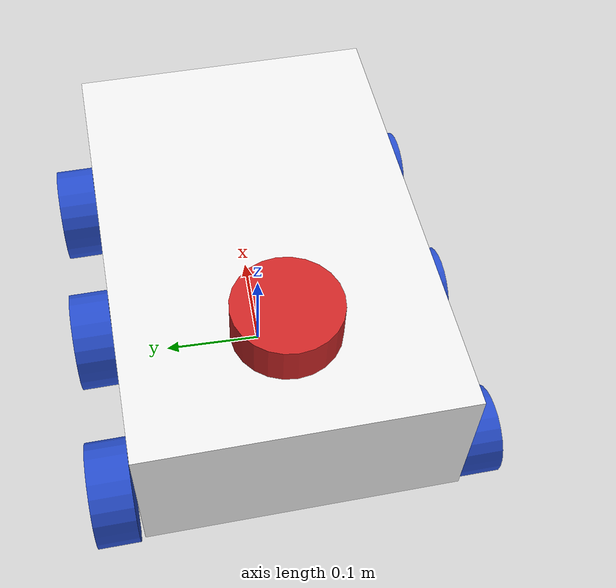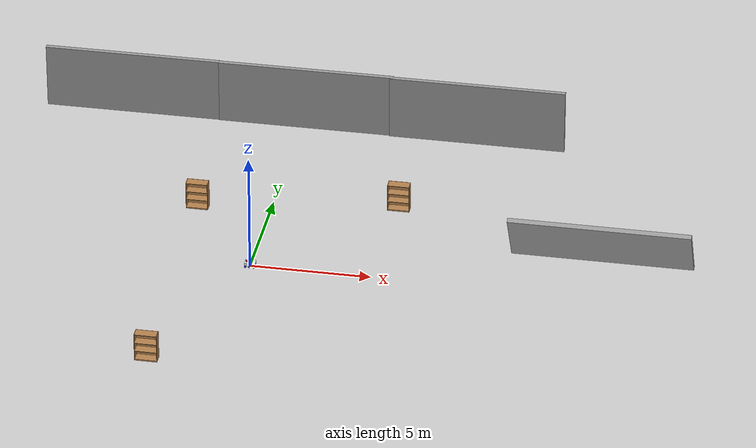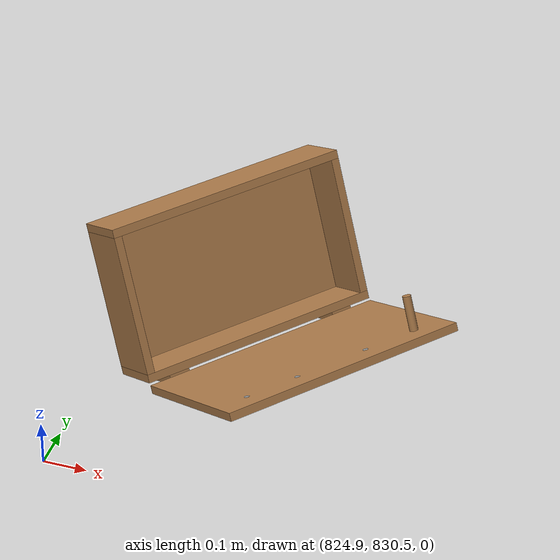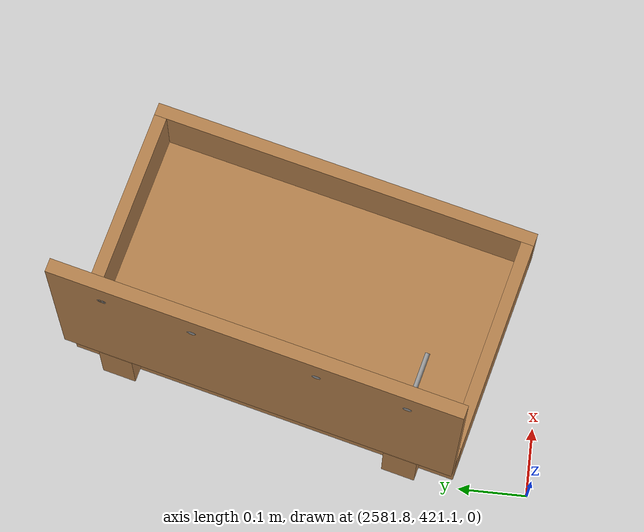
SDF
<sdf version="1.7">
 <world name="default">
  <light name="sun" type="directional">
   <pose>0 0 10 0 -0 0</pose>
   <diffuse>0.8 0.8 0.8 1</diffuse>
   <specular>0.2 0.2 0.2 1</specular>
   <attenuation>
    <range>1000</range>
    <constant>0.9</constant>
    <linear>0.01</linear>
    <quadratic>0.001</quadratic>
   </attenuation>
   <direction>-0.5 0.1 -0.9</direction>
   <spot><inner_angle>0</inner_angle><outer_angle>0</outer_angle><falloff>0</falloff></spot>
  </light>
  <gravity>0 0 -9.8</gravity>
  <magnetic_field>6e-06 2.3e-05 -4.2e-05</magnetic_field>
  <atmosphere type="adiabatic"/>
  <physics type="ode">
   <max_step_size>0.001</max_step_size>
   <real_time_factor>1</real_time_factor>
   <real_time_update_rate>1000</real_time_update_rate>
  </physics>
  <scene><ambient>0.4 0.4 0.4 1</ambient><background>0.7 0.7 0.7 1</background><shadows>1</shadows></scene>
  <audio><device>default</device></audio>
  <spherical_coordinates>
   <surface_model>EARTH_WGS84</surface_model>
   <latitude_deg>0</latitude_deg>
   <longitude_deg>0</longitude_deg>
   <elevation>0</elevation>
   <heading_deg>0</heading_deg>
  </spherical_coordinates>
  <model name="wooden_case_wooden_peg">
   <frame name="wooden_case::__model__" attached_to="wooden_case::base">
    <pose relative_to="__model__">0 0 0 0 -0 0</pose>
   </frame>
   <link name="wooden_case::base">
    <pose relative_to="wooden_case::__model__">0 0 0.024 0 -0 0</pose>
    <inertial>
     <pose>-0.022184 0 0.171592 0 -0 0</pose>
     <mass>3.96264</mass>
     <inertia>
      <ixx>0.213536</ixx>
      <ixy>0</ixy>
      <ixz>0.000779377</ixz>
      <iyy>0.0708943</iyy>
      <iyz>0</iyz>
      <izz>0.154604</izz>
     </inertia>
    </inertial>
    <collision name="collision_back">
     <pose>-0.053975 0 0.1778 0 -0 0</pose>
     <geometry><box><size>0.01905 0.5461 0.3175</size></box></geometry>
     <surface>
      <contact>
       <poissons_ratio>0.347</poissons_ratio>
       <elastic_modulus>8.8e+09</elastic_modulus>
       <ode><kp>100000</kp><kd>100</kd><max_vel>100</max_vel><min_depth>0.001</min_depth></ode>
      </contact>
      <friction>
       <torsional>
        <coefficient>1</coefficient>
        <use_patch_radius>0</use_patch_radius>
        <surface_radius>0.01</surface_radius>
       </torsional>
      </friction>
     </surface>
    </collision>
    <visual name="visual_back">
     <pose>-0.053975 0 0.1778 0 -0 0</pose>
     <geometry><box><size>0.01905 0.5461 0.3175</size></box></geometry>
     <material>
      <script><uri>file://media/materials/scripts/gazebo.material</uri><name>Gazebo/Wood</name></script>
     </material>
    </visual>
    <collision name="collision_bottom">
     <pose>0 0 0.009525 0 -0 0</pose>
     <geometry><box><size>0.127 0.5842 0.01905</size></box></geometry>
     <surface>
      <contact>
       <poissons_ratio>0.347</poissons_ratio>
       <elastic_modulus>8.8e+09</elastic_modulus>
       <ode><kp>100000</kp><kd>100</kd><max_vel>100</max_vel><min_depth>0.001</min_depth></ode>
      </contact>
      <friction>
       <torsional>
        <coefficient>1</coefficient>
        <use_patch_radius>0</use_patch_radius>
        <surface_radius>0.01</surface_radius>
       </torsional>
      </friction>
     </surface>
    </collision>
    <visual name="visual_bottom">
     <pose>0 0 0.009525 0 -0 0</pose>
     <geometry><box><size>0.127 0.5842 0.01905</size></box></geometry>
     <material>
      <script><uri>file://media/materials/scripts/gazebo.material</uri><name>Gazebo/Wood</name></script>
     </material>
    </visual>
    <collision name="collision_top">
     <pose>0 0 0.346075 0 -0 0</pose>
     <geometry><box><size>0.127 0.5842 0.01905</size></box></geometry>
     <surface>
      <contact>
       <poissons_ratio>0.347</poissons_ratio>
       <elastic_modulus>8.8e+09</elastic_modulus>
       <ode><kp>100000</kp><kd>100</kd><max_vel>100</max_vel><min_depth>0.001</min_depth></ode>
      </contact>
      <friction>
       <torsional>
        <coefficient>1</coefficient>
        <use_patch_radius>0</use_patch_radius>
        <surface_radius>0.01</surface_radius>
       </torsional>
      </friction>
     </surface>
    </collision>
    <visual name="visual_top">
     <pose>0 0 0.346075 0 -0 0</pose>
     <geometry><box><size>0.127 0.5842 0.01905</size></box></geometry>
     <material>
      <script><uri>file://media/materials/scripts/gazebo.material</uri><name>Gazebo/Wood</name></script>
     </material>
    </visual>
    <collision name="collision_left">
     <pose>0 -0.282575 0.1778 0 -0 0</pose>
     <geometry><box><size>0.127 0.01905 0.3175</size></box></geometry>
     <surface>
      <contact>
       <poissons_ratio>0.347</poissons_ratio>
       <elastic_modulus>8.8e+09</elastic_modulus>
       <ode><kp>100000</kp><kd>100</kd><max_vel>100</max_vel><min_depth>0.001</min_depth></ode>
      </contact>
      <friction>
       <torsional>
        <coefficient>1</coefficient>
        <use_patch_radius>0</use_patch_radius>
        <surface_radius>0.01</surface_radius>
       </torsional>
      </friction>
     </surface>
    </collision>
    <visual name="visual_left">
     <pose>0 -0.282575 0.1778 0 -0 0</pose>
     <geometry><box><size>0.127 0.01905 0.3175</size></box></geometry>
     <material>
      <script><uri>file://media/materials/scripts/gazebo.material</uri><name>Gazebo/Wood</name></script>
     </material>
    </visual>
    <collision name="collision_right">
     <pose>0 0.282575 0.1778 0 -0 0</pose>
     <geometry><box><size>0.127 0.01905 0.3175</size></box></geometry>
     <surface>
      <contact>
       <poissons_ratio>0.347</poissons_ratio>
       <elastic_modulus>8.8e+09</elastic_modulus>
       <ode><kp>100000</kp><kd>100</kd><max_vel>100</max_vel><min_depth>0.001</min_depth></ode>
      </contact>
      <friction>
       <torsional>
        <coefficient>1</coefficient>
        <use_patch_radius>0</use_patch_radius>
        <surface_radius>0.01</surface_radius>
       </torsional>
      </friction>
     </surface>
    </collision>
    <visual name="visual_right">
     <pose>0 0.282575 0.1778 0 -0 0</pose>
     <geometry><box><size>0.127 0.01905 0.3175</size></box></geometry>
     <material>
      <script><uri>file://media/materials/scripts/gazebo.material</uri><name>Gazebo/Wood</name></script>
     </material>
    </visual>
    <collision name="collision_block_left">
     <pose>0.0095 -0.2151 -0.012 0 -0 0</pose>
     <geometry><box><size>0.108 0.05 0.024</size></box></geometry>
     <surface>
      <contact>
       <poissons_ratio>0.347</poissons_ratio>
       <elastic_modulus>8.8e+09</elastic_modulus>
       <ode><kp>100000</kp><kd>100</kd><max_vel>100</max_vel><min_depth>0.001</min_depth></ode>
      </contact>
      <friction>
       <torsional>
        <coefficient>1</coefficient>
        <use_patch_radius>0</use_patch_radius>
        <surface_radius>0.01</surface_radius>
       </torsional>
      </friction>
     </surface>
    </collision>
    <visual name="visual_block_left">
     <pose>0.0095 -0.2151 -0.012 0 -0 0</pose>
     <geometry><box><size>0.108 0.05 0.024</size></box></geometry>
     <material>
      <script><uri>file://media/materials/scripts/gazebo.material</uri><name>Gazebo/Wood</name></script>
     </material>
    </visual>
    <collision name="collision_block_right">
     <pose>0.0095 0.2151 -0.012 0 -0 0</pose>
     <geometry><box><size>0.108 0.05 0.024</size></box></geometry>
     <surface>
      <contact>
       <poissons_ratio>0.347</poissons_ratio>
       <elastic_modulus>8.8e+09</elastic_modulus>
       <ode><kp>100000</kp><kd>100</kd><max_vel>100</max_vel><min_depth>0.001</min_depth></ode>
      </contact>
      <friction>
       <torsional>
        <coefficient>1</coefficient>
        <use_patch_radius>0</use_patch_radius>
        <surface_radius>0.01</surface_radius>
       </torsional>
      </friction>
     </surface>
    </collision>
    <visual name="visual_block_right">
     <pose>0.0095 0.2151 -0.012 0 -0 0</pose>
     <geometry><box><size>0.108 0.05 0.024</size></box></geometry>
     <material>
      <script><uri>file://media/materials/scripts/gazebo.material</uri><name>Gazebo/Wood</name></script>
     </material>
    </visual>
   </link>
   <link name="wooden_case::lid">
    <pose relative_to="wooden_case::__model__">0.243775 0 0.009525 0 -0 0</pose>
    <inertial>
     <mass>1.97874</mass>
     <inertia>
      <ixx>0.0563367</ixx>
      <ixy>0</ixy>
      <ixz>0</ixz>
      <iyy>0.020911</iyy>
      <iyz>0</iyz>
      <izz>0.0771281</izz>
     </inertia>
    </inertial>
    <collision name="collision">
     <geometry><box><size>0.3556 0.5842 0.01905</size></box></geometry>
     <surface>
      <contact>
       <poissons_ratio>0.347</poissons_ratio>
       <elastic_modulus>8.8e+09</elastic_modulus>
       <ode><kp>100000</kp><kd>100</kd><max_vel>100</max_vel><min_depth>0.001</min_depth></ode>
      </contact>
      <friction>
       <torsional>
        <coefficient>1</coefficient>
        <use_patch_radius>0</use_patch_radius>
        <surface_radius>0.01</surface_radius>
       </torsional>
      </friction>
     </surface>
    </collision>
    <visual name="visual">
     <geometry><box><size>0.3556 0.5842 0.01905</size></box></geometry>
     <material>
      <script><uri>file://media/materials/scripts/gazebo.material</uri><name>Gazebo/Wood</name></script>
     </material>
    </visual>
    <visual name="tee_nut_1">
     <pose>0.122 -0.216 0 0 -0 0</pose>
     <geometry><cylinder><radius>0.00635</radius><length>0.0192405</length></cylinder></geometry>
     <material>
      <script><uri>file://media/materials/scripts/gazebo.material</uri><name>Gazebo/Grey</name></script>
     </material>
    </visual>
    <visual name="tee_nut_2">
     <pose>0.122 -0.088 0 0 -0 0</pose>
     <geometry><cylinder><radius>0.00635</radius><length>0.0192405</length></cylinder></geometry>
     <material>
      <script><uri>file://media/materials/scripts/gazebo.material</uri><name>Gazebo/Grey</name></script>
     </material>
    </visual>
    <visual name="tee_nut_3">
     <pose>0.122 0.088 0 0 -0 0</pose>
     <geometry><cylinder><radius>0.00635</radius><length>0.0192405</length></cylinder></geometry>
     <material>
      <script><uri>file://media/materials/scripts/gazebo.material</uri><name>Gazebo/Grey</name></script>
     </material>
    </visual>
    <visual name="tee_nut_4">
     <pose>0.122 0.216 0 0 -0 0</pose>
     <geometry><cylinder><radius>0.00635</radius><length>0.0192405</length></cylinder></geometry>
     <material>
      <script><uri>file://media/materials/scripts/gazebo.material</uri><name>Gazebo/Grey</name></script>
     </material>
    </visual>
   </link>
   <joint name="wooden_case::lid_hinge" type="revolute">
    <pose>-0.1778 0 0.01905 0 -0 0</pose>
    <parent>wooden_case::base</parent>
    <child>wooden_case::lid</child>
    <axis>
     <xyz>0 1 0</xyz>
     <limit><upper>0.523599</upper><lower>-1.5708</lower></limit>
     <dynamics><spring_reference>0</spring_reference><spring_stiffness>0</spring_stiffness></dynamics>
    </axis>
   </joint>
   <frame name="peg::__model__" attached_to="peg::link">
    <pose relative_to="__model__">0.365774 0.216 0.01905 0 -0 0</pose>
   </frame>
   <link name="peg::link">
    <pose relative_to="peg::__model__">0 0 0.04 0 -0 0</pose>
    <inertial>
     <mass>0.0175</mass>
     <inertia>
      <ixx>9.74923e-06</ixx>
      <ixy>0</ixy>
      <ixz>0</ixz>
      <iyy>9.74923e-06</iyy>
      <iyz>0</iyz>
      <izz>8.31797e-07</izz>
     </inertia>
    </inertial>
    <collision name="collision">
     <geometry><cylinder><radius>0.00975</radius><length>0.08</length></cylinder></geometry>
     <surface>
      <contact>
       <poissons_ratio>0.347</poissons_ratio>
       <elastic_modulus>8.8e+09</elastic_modulus>
       <ode><kp>100000</kp><kd>100</kd><max_vel>100</max_vel><min_depth>0.001</min_depth></ode>
      </contact>
      <friction>
       <torsional>
        <coefficient>1</coefficient>
        <use_patch_radius>0</use_patch_radius>
        <surface_radius>0.01</surface_radius>
       </torsional>
      </friction>
     </surface>
    </collision>
    <visual name="visual">
     <geometry><cylinder><radius>0.00975</radius><length>0.08</length></cylinder></geometry>
     <material>
      <script><uri>file://media/materials/scripts/gazebo.material</uri><name>Gazebo/Wood</name></script>
     </material>
    </visual>
   </link>
   <joint name="case_peg" type="revolute">
    <child>peg::link</child>
    <parent>wooden_case::lid</parent>
    <axis>
     <xyz>0 0 1</xyz>
     <limit><upper>0</upper><lower>0</lower></limit>
     <dynamics><spring_reference>0</spring_reference><spring_stiffness>0</spring_stiffness></dynamics>
    </axis>
   </joint>
   <pose>1022.39 268.785 -0.001057 -1e-06 -0.000434 -1.73981</pose>
  </model>
  <model name="wooden_case_metal_peg">
   <frame name="wooden_case::__model__" attached_to="wooden_case::base">
    <pose relative_to="__model__">0 0 0 0 -0 0</pose>
   </frame>
   <link name="wooden_case::base">
    <pose relative_to="wooden_case::__model__">0 0 0.024 0 -0 0</pose>
    <inertial>
     <pose>-0.022184 0 0.171592 0 -0 0</pose>
     <mass>3.96264</mass>
     <inertia>
      <ixx>0.213536</ixx>
      <ixy>0</ixy>
      <ixz>0.000779377</ixz>
      <iyy>0.0708943</iyy>
      <iyz>0</iyz>
      <izz>0.154604</izz>
     </inertia>
    </inertial>
    <collision name="collision_back">
     <pose>-0.053975 0 0.1778 0 -0 0</pose>
     <geometry><box><size>0.01905 0.5461 0.3175</size></box></geometry>
     <surface>
      <contact>
       <poissons_ratio>0.347</poissons_ratio>
       <elastic_modulus>8.8e+09</elastic_modulus>
       <ode><kp>100000</kp><kd>100</kd><max_vel>100</max_vel><min_depth>0.001</min_depth></ode>
      </contact>
      <friction>
       <torsional>
        <coefficient>1</coefficient>
        <use_patch_radius>0</use_patch_radius>
        <surface_radius>0.01</surface_radius>
       </torsional>
      </friction>
     </surface>
    </collision>
    <visual name="visual_back">
     <pose>-0.053975 0 0.1778 0 -0 0</pose>
     <geometry><box><size>0.01905 0.5461 0.3175</size></box></geometry>
     <material>
      <script><uri>file://media/materials/scripts/gazebo.material</uri><name>Gazebo/Wood</name></script>
     </material>
    </visual>
    <collision name="collision_bottom">
     <pose>0 0 0.009525 0 -0 0</pose>
     <geometry><box><size>0.127 0.5842 0.01905</size></box></geometry>
     <surface>
      <contact>
       <poissons_ratio>0.347</poissons_ratio>
       <elastic_modulus>8.8e+09</elastic_modulus>
       <ode><kp>100000</kp><kd>100</kd><max_vel>100</max_vel><min_depth>0.001</min_depth></ode>
      </contact>
      <friction>
       <torsional>
        <coefficient>1</coefficient>
        <use_patch_radius>0</use_patch_radius>
        <surface_radius>0.01</surface_radius>
       </torsional>
      </friction>
     </surface>
    </collision>
    <visual name="visual_bottom">
     <pose>0 0 0.009525 0 -0 0</pose>
     <geometry><box><size>0.127 0.5842 0.01905</size></box></geometry>
     <material>
      <script><uri>file://media/materials/scripts/gazebo.material</uri><name>Gazebo/Wood</name></script>
     </material>
    </visual>
    <collision name="collision_top">
     <pose>0 0 0.346075 0 -0 0</pose>
     <geometry><box><size>0.127 0.5842 0.01905</size></box></geometry>
     <surface>
      <contact>
       <poissons_ratio>0.347</poissons_ratio>
       <elastic_modulus>8.8e+09</elastic_modulus>
       <ode><kp>100000</kp><kd>100</kd><max_vel>100</max_vel><min_depth>0.001</min_depth></ode>
      </contact>
      <friction>
       <torsional>
        <coefficient>1</coefficient>
        <use_patch_radius>0</use_patch_radius>
        <surface_radius>0.01</surface_radius>
       </torsional>
      </friction>
     </surface>
    </collision>
    <visual name="visual_top">
     <pose>0 0 0.346075 0 -0 0</pose>
     <geometry><box><size>0.127 0.5842 0.01905</size></box></geometry>
     <material>
      <script><uri>file://media/materials/scripts/gazebo.material</uri><name>Gazebo/Wood</name></script>
     </material>
    </visual>
    <collision name="collision_left">
     <pose>0 -0.282575 0.1778 0 -0 0</pose>
     <geometry><box><size>0.127 0.01905 0.3175</size></box></geometry>
     <surface>
      <contact>
       <poissons_ratio>0.347</poissons_ratio>
       <elastic_modulus>8.8e+09</elastic_modulus>
       <ode><kp>100000</kp><kd>100</kd><max_vel>100</max_vel><min_depth>0.001</min_depth></ode>
      </contact>
      <friction>
       <torsional>
        <coefficient>1</coefficient>
        <use_patch_radius>0</use_patch_radius>
        <surface_radius>0.01</surface_radius>
       </torsional>
      </friction>
     </surface>
    </collision>
    <visual name="visual_left">
     <pose>0 -0.282575 0.1778 0 -0 0</pose>
     <geometry><box><size>0.127 0.01905 0.3175</size></box></geometry>
     <material>
      <script><uri>file://media/materials/scripts/gazebo.material</uri><name>Gazebo/Wood</name></script>
     </material>
    </visual>
    <collision name="collision_right">
     <pose>0 0.282575 0.1778 0 -0 0</pose>
     <geometry><box><size>0.127 0.01905 0.3175</size></box></geometry>
     <surface>
      <contact>
       <poissons_ratio>0.347</poissons_ratio>
       <elastic_modulus>8.8e+09</elastic_modulus>
       <ode><kp>100000</kp><kd>100</kd><max_vel>100</max_vel><min_depth>0.001</min_depth></ode>
      </contact>
      <friction>
       <torsional>
        <coefficient>1</coefficient>
        <use_patch_radius>0</use_patch_radius>
        <surface_radius>0.01</surface_radius>
       </torsional>
      </friction>
     </surface>
    </collision>
    <visual name="visual_right">
     <pose>0 0.282575 0.1778 0 -0 0</pose>
     <geometry><box><size>0.127 0.01905 0.3175</size></box></geometry>
     <material>
      <script><uri>file://media/materials/scripts/gazebo.material</uri><name>Gazebo/Wood</name></script>
     </material>
    </visual>
    <collision name="collision_block_left">
     <pose>0.0095 -0.2151 -0.012 0 -0 0</pose>
     <geometry><box><size>0.108 0.05 0.024</size></box></geometry>
     <surface>
      <contact>
       <poissons_ratio>0.347</poissons_ratio>
       <elastic_modulus>8.8e+09</elastic_modulus>
       <ode><kp>100000</kp><kd>100</kd><max_vel>100</max_vel><min_depth>0.001</min_depth></ode>
      </contact>
      <friction>
       <torsional>
        <coefficient>1</coefficient>
        <use_patch_radius>0</use_patch_radius>
        <surface_radius>0.01</surface_radius>
       </torsional>
      </friction>
     </surface>
    </collision>
    <visual name="visual_block_left">
     <pose>0.0095 -0.2151 -0.012 0 -0 0</pose>
     <geometry><box><size>0.108 0.05 0.024</size></box></geometry>
     <material>
      <script><uri>file://media/materials/scripts/gazebo.material</uri><name>Gazebo/Wood</name></script>
     </material>
    </visual>
    <collision name="collision_block_right">
     <pose>0.0095 0.2151 -0.012 0 -0 0</pose>
     <geometry><box><size>0.108 0.05 0.024</size></box></geometry>
     <surface>
      <contact>
       <poissons_ratio>0.347</poissons_ratio>
       <elastic_modulus>8.8e+09</elastic_modulus>
       <ode><kp>100000</kp><kd>100</kd><max_vel>100</max_vel><min_depth>0.001</min_depth></ode>
      </contact>
      <friction>
       <torsional>
        <coefficient>1</coefficient>
        <use_patch_radius>0</use_patch_radius>
        <surface_radius>0.01</surface_radius>
       </torsional>
      </friction>
     </surface>
    </collision>
    <visual name="visual_block_right">
     <pose>0.0095 0.2151 -0.012 0 -0 0</pose>
     <geometry><box><size>0.108 0.05 0.024</size></box></geometry>
     <material>
      <script><uri>file://media/materials/scripts/gazebo.material</uri><name>Gazebo/Wood</name></script>
     </material>
    </visual>
   </link>
   <link name="wooden_case::lid">
    <pose relative_to="wooden_case::__model__">0.243775 0 0.009525 0 -0 0</pose>
    <inertial>
     <mass>1.97874</mass>
     <inertia>
      <ixx>0.0563367</ixx>
      <ixy>0</ixy>
      <ixz>0</ixz>
      <iyy>0.020911</iyy>
      <iyz>0</iyz>
      <izz>0.0771281</izz>
     </inertia>
    </inertial>
    <collision name="collision">
     <geometry><box><size>0.3556 0.5842 0.01905</size></box></geometry>
     <surface>
      <contact>
       <poissons_ratio>0.347</poissons_ratio>
       <elastic_modulus>8.8e+09</elastic_modulus>
       <ode><kp>100000</kp><kd>100</kd><max_vel>100</max_vel><min_depth>0.001</min_depth></ode>
      </contact>
      <friction>
       <torsional>
        <coefficient>1</coefficient>
        <use_patch_radius>0</use_patch_radius>
        <surface_radius>0.01</surface_radius>
       </torsional>
      </friction>
     </surface>
    </collision>
    <visual name="visual">
     <geometry><box><size>0.3556 0.5842 0.01905</size></box></geometry>
     <material>
      <script><uri>file://media/materials/scripts/gazebo.material</uri><name>Gazebo/Wood</name></script>
     </material>
    </visual>
    <visual name="tee_nut_1">
     <pose>0.122 -0.216 0 0 -0 0</pose>
     <geometry><cylinder><radius>0.00635</radius><length>0.0192405</length></cylinder></geometry>
     <material>
      <script><uri>file://media/materials/scripts/gazebo.material</uri><name>Gazebo/Grey</name></script>
     </material>
    </visual>
    <visual name="tee_nut_2">
     <pose>0.122 -0.088 0 0 -0 0</pose>
     <geometry><cylinder><radius>0.00635</radius><length>0.0192405</length></cylinder></geometry>
     <material>
      <script><uri>file://media/materials/scripts/gazebo.material</uri><name>Gazebo/Grey</name></script>
     </material>
    </visual>
    <visual name="tee_nut_3">
     <pose>0.122 0.088 0 0 -0 0</pose>
     <geometry><cylinder><radius>0.00635</radius><length>0.0192405</length></cylinder></geometry>
     <material>
      <script><uri>file://media/materials/scripts/gazebo.material</uri><name>Gazebo/Grey</name></script>
     </material>
    </visual>
    <visual name="tee_nut_4">
     <pose>0.122 0.216 0 0 -0 0</pose>
     <geometry><cylinder><radius>0.00635</radius><length>0.0192405</length></cylinder></geometry>
     <material>
      <script><uri>file://media/materials/scripts/gazebo.material</uri><name>Gazebo/Grey</name></script>
     </material>
    </visual>
   </link>
   <joint name="wooden_case::lid_hinge" type="revolute">
    <pose>-0.1778 0 0.01905 0 -0 0</pose>
    <parent>wooden_case::base</parent>
    <child>wooden_case::lid</child>
    <axis>
     <xyz>0 1 0</xyz>
     <limit><upper>0.523599</upper><lower>-1.5708</lower></limit>
     <dynamics><spring_reference>0</spring_reference><spring_stiffness>0</spring_stiffness></dynamics>
    </axis>
   </joint>
   <frame name="peg::__model__" attached_to="peg::link">
    <pose relative_to="__model__">0.365774 0.216 0.01905 0 -0 0</pose>
   </frame>
   <link name="peg::link">
    <pose relative_to="peg::__model__">0 0 0.031 0 -0 0</pose>
    <inertial>
     <mass>0.0121</mass>
     <inertia>
      <ixx>3.90898e-06</ixx>
      <ixy>0</ixy>
      <ixz>0</ixz>
      <iyy>3.90898e-06</iyy>
      <iyz>0</iyz>
      <izz>6.58845e-08</izz>
     </inertia>
    </inertial>
    <collision name="collision">
     <geometry><cylinder><radius>0.0033</radius><length>0.062</length></cylinder></geometry>
     <surface>
      <contact>
       <poissons_ratio>0.305</poissons_ratio>
       <elastic_modulus>2e+11</elastic_modulus>
       <ode><kp>100000</kp><kd>100</kd><max_vel>100</max_vel><min_depth>0.001</min_depth></ode>
      </contact>
      <friction>
       <torsional>
        <coefficient>1</coefficient>
        <use_patch_radius>0</use_patch_radius>
        <surface_radius>0.01</surface_radius>
       </torsional>
      </friction>
     </surface>
    </collision>
    <visual name="visual">
     <geometry><cylinder><radius>0.0033</radius><length>0.062</length></cylinder></geometry>
     <material>
      <script><uri>file://media/materials/scripts/gazebo.material</uri><name>Gazebo/Grey</name></script>
     </material>
    </visual>
   </link>
   <joint name="case_peg" type="revolute">
    <child>peg::link</child>
    <parent>wooden_case::lid</parent>
    <axis>
     <xyz>0 0 1</xyz>
     <limit><upper>0</upper><lower>0</lower></limit>
     <dynamics><spring_reference>0</spring_reference><spring_stiffness>0</spring_stiffness></dynamics>
    </axis>
   </joint>
   <pose>1058.32 851.762 0.093399 -0.026544 1.57077 -2.38321</pose>
  </model>
  <model name="wooden_case_wooden_peg_0">
   <frame name="wooden_case::__model__" attached_to="wooden_case::base">
    <pose relative_to="__model__">0 0 0 0 -0 0</pose>
   </frame>
   <link name="wooden_case::base">
    <pose relative_to="wooden_case::__model__">0 0 0.024 0 -0 0</pose>
    <inertial>
     <pose>-0.022184 0 0.171592 0 -0 0</pose>
     <mass>3.96264</mass>
     <inertia>
      <ixx>0.213536</ixx>
      <ixy>0</ixy>
      <ixz>0.000779377</ixz>
      <iyy>0.0708943</iyy>
      <iyz>0</iyz>
      <izz>0.154604</izz>
     </inertia>
    </inertial>
    <collision name="collision_back">
     <pose>-0.053975 0 0.1778 0 -0 0</pose>
     <geometry><box><size>0.01905 0.5461 0.3175</size></box></geometry>
     <surface>
      <contact>
       <poissons_ratio>0.347</poissons_ratio>
       <elastic_modulus>8.8e+09</elastic_modulus>
       <ode><kp>100000</kp><kd>100</kd><max_vel>100</max_vel><min_depth>0.001</min_depth></ode>
      </contact>
      <friction>
       <torsional>
        <coefficient>1</coefficient>
        <use_patch_radius>0</use_patch_radius>
        <surface_radius>0.01</surface_radius>
       </torsional>
      </friction>
     </surface>
    </collision>
    <visual name="visual_back">
     <pose>-0.053975 0 0.1778 0 -0 0</pose>
     <geometry><box><size>0.01905 0.5461 0.3175</size></box></geometry>
     <material>
      <script><uri>file://media/materials/scripts/gazebo.material</uri><name>Gazebo/Wood</name></script>
     </material>
    </visual>
    <collision name="collision_bottom">
     <pose>0 0 0.009525 0 -0 0</pose>
     <geometry><box><size>0.127 0.5842 0.01905</size></box></geometry>
     <surface>
      <contact>
       <poissons_ratio>0.347</poissons_ratio>
       <elastic_modulus>8.8e+09</elastic_modulus>
       <ode><kp>100000</kp><kd>100</kd><max_vel>100</max_vel><min_depth>0.001</min_depth></ode>
      </contact>
      <friction>
       <torsional>
        <coefficient>1</coefficient>
        <use_patch_radius>0</use_patch_radius>
        <surface_radius>0.01</surface_radius>
       </torsional>
      </friction>
     </surface>
    </collision>
    <visual name="visual_bottom">
     <pose>0 0 0.009525 0 -0 0</pose>
     <geometry><box><size>0.127 0.5842 0.01905</size></box></geometry>
     <material>
      <script><uri>file://media/materials/scripts/gazebo.material</uri><name>Gazebo/Wood</name></script>
     </material>
    </visual>
    <collision name="collision_top">
     <pose>0 0 0.346075 0 -0 0</pose>
     <geometry><box><size>0.127 0.5842 0.01905</size></box></geometry>
     <surface>
      <contact>
       <poissons_ratio>0.347</poissons_ratio>
       <elastic_modulus>8.8e+09</elastic_modulus>
       <ode><kp>100000</kp><kd>100</kd><max_vel>100</max_vel><min_depth>0.001</min_depth></ode>
      </contact>
      <friction>
       <torsional>
        <coefficient>1</coefficient>
        <use_patch_radius>0</use_patch_radius>
        <surface_radius>0.01</surface_radius>
       </torsional>
      </friction>
     </surface>
    </collision>
    <visual name="visual_top">
     <pose>0 0 0.346075 0 -0 0</pose>
     <geometry><box><size>0.127 0.5842 0.01905</size></box></geometry>
     <material>
      <script><uri>file://media/materials/scripts/gazebo.material</uri><name>Gazebo/Wood</name></script>
     </material>
    </visual>
    <collision name="collision_left">
     <pose>0 -0.282575 0.1778 0 -0 0</pose>
     <geometry><box><size>0.127 0.01905 0.3175</size></box></geometry>
     <surface>
      <contact>
       <poissons_ratio>0.347</poissons_ratio>
       <elastic_modulus>8.8e+09</elastic_modulus>
       <ode><kp>100000</kp><kd>100</kd><max_vel>100</max_vel><min_depth>0.001</min_depth></ode>
      </contact>
      <friction>
       <torsional>
        <coefficient>1</coefficient>
        <use_patch_radius>0</use_patch_radius>
        <surface_radius>0.01</surface_radius>
       </torsional>
      </friction>
     </surface>
    </collision>
    <visual name="visual_left">
     <pose>0 -0.282575 0.1778 0 -0 0</pose>
     <geometry><box><size>0.127 0.01905 0.3175</size></box></geometry>
     <material>
      <script><uri>file://media/materials/scripts/gazebo.material</uri><name>Gazebo/Wood</name></script>
     </material>
    </visual>
    <collision name="collision_right">
     <pose>0 0.282575 0.1778 0 -0 0</pose>
     <geometry><box><size>0.127 0.01905 0.3175</size></box></geometry>
     <surface>
      <contact>
       <poissons_ratio>0.347</poissons_ratio>
       <elastic_modulus>8.8e+09</elastic_modulus>
       <ode><kp>100000</kp><kd>100</kd><max_vel>100</max_vel><min_depth>0.001</min_depth></ode>
      </contact>
      <friction>
       <torsional>
        <coefficient>1</coefficient>
        <use_patch_radius>0</use_patch_radius>
        <surface_radius>0.01</surface_radius>
       </torsional>
      </friction>
     </surface>
    </collision>
    <visual name="visual_right">
     <pose>0 0.282575 0.1778 0 -0 0</pose>
     <geometry><box><size>0.127 0.01905 0.3175</size></box></geometry>
     <material>
      <script><uri>file://media/materials/scripts/gazebo.material</uri><name>Gazebo/Wood</name></script>
     </material>
    </visual>
    <collision name="collision_block_left">
     <pose>0.0095 -0.2151 -0.012 0 -0 0</pose>
     <geometry><box><size>0.108 0.05 0.024</size></box></geometry>
     <surface>
      <contact>
       <poissons_ratio>0.347</poissons_ratio>
       <elastic_modulus>8.8e+09</elastic_modulus>
       <ode><kp>100000</kp><kd>100</kd><max_vel>100</max_vel><min_depth>0.001</min_depth></ode>
      </contact>
      <friction>
       <torsional>
        <coefficient>1</coefficient>
        <use_patch_radius>0</use_patch_radius>
        <surface_radius>0.01</surface_radius>
       </torsional>
      </friction>
     </surface>
    </collision>
    <visual name="visual_block_left">
     <pose>0.0095 -0.2151 -0.012 0 -0 0</pose>
     <geometry><box><size>0.108 0.05 0.024</size></box></geometry>
     <material>
      <script><uri>file://media/materials/scripts/gazebo.material</uri><name>Gazebo/Wood</name></script>
     </material>
    </visual>
    <collision name="collision_block_right">
     <pose>0.0095 0.2151 -0.012 0 -0 0</pose>
     <geometry><box><size>0.108 0.05 0.024</size></box></geometry>
     <surface>
      <contact>
       <poissons_ratio>0.347</poissons_ratio>
       <elastic_modulus>8.8e+09</elastic_modulus>
       <ode><kp>100000</kp><kd>100</kd><max_vel>100</max_vel><min_depth>0.001</min_depth></ode>
      </contact>
      <friction>
       <torsional>
        <coefficient>1</coefficient>
        <use_patch_radius>0</use_patch_radius>
        <surface_radius>0.01</surface_radius>
       </torsional>
      </friction>
     </surface>
    </collision>
    <visual name="visual_block_right">
     <pose>0.0095 0.2151 -0.012 0 -0 0</pose>
     <geometry><box><size>0.108 0.05 0.024</size></box></geometry>
     <material>
      <script><uri>file://media/materials/scripts/gazebo.material</uri><name>Gazebo/Wood</name></script>
     </material>
    </visual>
   </link>
   <link name="wooden_case::lid">
    <pose relative_to="wooden_case::__model__">0.243775 0 0.009525 0 -0 0</pose>
    <inertial>
     <mass>1.97874</mass>
     <inertia>
      <ixx>0.0563367</ixx>
      <ixy>0</ixy>
      <ixz>0</ixz>
      <iyy>0.020911</iyy>
      <iyz>0</iyz>
      <izz>0.0771281</izz>
     </inertia>
    </inertial>
    <collision name="collision">
     <geometry><box><size>0.3556 0.5842 0.01905</size></box></geometry>
     <surface>
      <contact>
       <poissons_ratio>0.347</poissons_ratio>
       <elastic_modulus>8.8e+09</elastic_modulus>
       <ode><kp>100000</kp><kd>100</kd><max_vel>100</max_vel><min_depth>0.001</min_depth></ode>
      </contact>
      <friction>
       <torsional>
        <coefficient>1</coefficient>
        <use_patch_radius>0</use_patch_radius>
        <surface_radius>0.01</surface_radius>
       </torsional>
      </friction>
     </surface>
    </collision>
    <visual name="visual">
     <geometry><box><size>0.3556 0.5842 0.01905</size></box></geometry>
     <material>
      <script><uri>file://media/materials/scripts/gazebo.material</uri><name>Gazebo/Wood</name></script>
     </material>
    </visual>
    <visual name="tee_nut_1">
     <pose>0.122 -0.216 0 0 -0 0</pose>
     <geometry><cylinder><radius>0.00635</radius><length>0.0192405</length></cylinder></geometry>
     <material>
      <script><uri>file://media/materials/scripts/gazebo.material</uri><name>Gazebo/Grey</name></script>
     </material>
    </visual>
    <visual name="tee_nut_2">
     <pose>0.122 -0.088 0 0 -0 0</pose>
     <geometry><cylinder><radius>0.00635</radius><length>0.0192405</length></cylinder></geometry>
     <material>
      <script><uri>file://media/materials/scripts/gazebo.material</uri><name>Gazebo/Grey</name></script>
     </material>
    </visual>
    <visual name="tee_nut_3">
     <pose>0.122 0.088 0 0 -0 0</pose>
     <geometry><cylinder><radius>0.00635</radius><length>0.0192405</length></cylinder></geometry>
     <material>
      <script><uri>file://media/materials/scripts/gazebo.material</uri><name>Gazebo/Grey</name></script>
     </material>
    </visual>
    <visual name="tee_nut_4">
     <pose>0.122 0.216 0 0 -0 0</pose>
     <geometry><cylinder><radius>0.00635</radius><length>0.0192405</length></cylinder></geometry>
     <material>
      <script><uri>file://media/materials/scripts/gazebo.material</uri><name>Gazebo/Grey</name></script>
     </material>
    </visual>
   </link>
   <joint name="wooden_case::lid_hinge" type="revolute">
    <pose>-0.1778 0 0.01905 0 -0 0</pose>
    <parent>wooden_case::base</parent>
    <child>wooden_case::lid</child>
    <axis>
     <xyz>0 1 0</xyz>
     <limit><upper>0.523599</upper><lower>-1.5708</lower></limit>
     <dynamics><spring_reference>0</spring_reference><spring_stiffness>0</spring_stiffness></dynamics>
    </axis>
   </joint>
   <frame name="peg::__model__" attached_to="peg::link">
    <pose relative_to="__model__">0.365774 0.216 0.01905 0 -0 0</pose>
   </frame>
   <link name="peg::link">
    <pose relative_to="peg::__model__">0 0 0.04 0 -0 0</pose>
    <inertial>
     <mass>0.0175</mass>
     <inertia>
      <ixx>9.74923e-06</ixx>
      <ixy>0</ixy>
      <ixz>0</ixz>
      <iyy>9.74923e-06</iyy>
      <iyz>0</iyz>
      <izz>8.31797e-07</izz>
     </inertia>
    </inertial>
    <collision name="collision">
     <geometry><cylinder><radius>0.00975</radius><length>0.08</length></cylinder></geometry>
     <surface>
      <contact>
       <poissons_ratio>0.347</poissons_ratio>
       <elastic_modulus>8.8e+09</elastic_modulus>
       <ode><kp>100000</kp><kd>100</kd><max_vel>100</max_vel><min_depth>0.001</min_depth></ode>
      </contact>
      <friction>
       <torsional>
        <coefficient>1</coefficient>
        <use_patch_radius>0</use_patch_radius>
        <surface_radius>0.01</surface_radius>
       </torsional>
      </friction>
     </surface>
    </collision>
    <visual name="visual">
     <geometry><cylinder><radius>0.00975</radius><length>0.08</length></cylinder></geometry>
     <material>
      <script><uri>file://media/materials/scripts/gazebo.material</uri><name>Gazebo/Wood</name></script>
     </material>
    </visual>
   </link>
   <joint name="case_peg" type="revolute">
    <child>peg::link</child>
    <parent>wooden_case::lid</parent>
    <axis>
     <xyz>0 0 1</xyz>
     <limit><upper>0</upper><lower>0</lower></limit>
     <dynamics><spring_reference>0</spring_reference><spring_stiffness>0</spring_stiffness></dynamics>
    </axis>
   </joint>
   <pose>801.996 1175.96 0.06247 -0.092463 -1.57079 2.92648</pose>
  </model>
  <model name="bookshelf">
   <static>1</static>
   <link name="link">
    <inertial><mass>1</mass></inertial>
    <collision name="back">
     <pose>0 0.005 0.6 0 -0 0</pose>
     <geometry><box><size>0.9 0.01 1.2</size></box></geometry>
    </collision>
    <visual name="visual1">
     <pose>0 0.005 0.6 0 -0 0</pose>
     <geometry><box><size>0.9 0.01 1.2</size></box></geometry>
     <material>
      <script><uri>file://media/materials/scripts/gazebo.material</uri><name>Gazebo/Wood</name></script>
     </material>
    </visual>
    <collision name="left_side">
     <pose>0.45 -0.195 0.6 0 -0 0</pose>
     <geometry><box><size>0.02 0.4 1.2</size></box></geometry>
    </collision>
    <visual name="visual2">
     <pose>0.45 -0.195 0.6 0 -0 0</pose>
     <geometry><box><size>0.02 0.4 1.2</size></box></geometry>
     <material>
      <script><uri>file://media/materials/scripts/gazebo.material</uri><name>Gazebo/Wood</name></script>
     </material>
    </visual>
    <collision name="right_side">
     <pose>-0.45 -0.195 0.6 0 -0 0</pose>
     <geometry><box><size>0.02 0.4 1.2</size></box></geometry>
    </collision>
    <visual name="visual3">
     <pose>-0.45 -0.195 0.6 0 -0 0</pose>
     <geometry><box><size>0.02 0.4 1.2</size></box></geometry>
     <material>
      <script><uri>file://media/materials/scripts/gazebo.material</uri><name>Gazebo/Wood</name></script>
     </material>
    </visual>
    <collision name="bottom">
     <pose>0 -0.195 0.03 0 -0 0</pose>
     <geometry><box><size>0.88 0.4 0.06</size></box></geometry>
    </collision>
    <visual name="visual4">
     <pose>0 -0.195 0.03 0 -0 0</pose>
     <geometry><box><size>0.88 0.4 0.06</size></box></geometry>
     <material>
      <script><uri>file://media/materials/scripts/gazebo.material</uri><name>Gazebo/Wood</name></script>
     </material>
    </visual>
    <collision name="top">
     <pose>0 -0.195 1.19 0 -0 0</pose>
     <geometry><box><size>0.88 0.4 0.02</size></box></geometry>
    </collision>
    <visual name="visual5">
     <pose>0 -0.195 1.19 0 -0 0</pose>
     <geometry><box><size>0.88 0.4 0.02</size></box></geometry>
     <material>
      <script><uri>file://media/materials/scripts/gazebo.material</uri><name>Gazebo/Wood</name></script>
     </material>
    </visual>
    <collision name="low_shelf">
     <pose>0 -0.195 0.43 0 -0 0</pose>
     <geometry><box><size>0.88 0.4 0.02</size></box></geometry>
    </collision>
    <visual name="visual6">
     <pose>0 -0.195 0.43 0 -0 0</pose>
     <geometry><box><size>0.88 0.4 0.02</size></box></geometry>
     <material>
      <script><uri>file://media/materials/scripts/gazebo.material</uri><name>Gazebo/Wood</name></script>
     </material>
    </visual>
    <collision name="high_shelf">
     <pose>0 -0.195 0.8 0 -0 0</pose>
     <geometry><box><size>0.88 0.4 0.02</size></box></geometry>
    </collision>
    <visual name="visual7">
     <pose>0 -0.195 0.8 0 -0 0</pose>
     <geometry><box><size>0.88 0.4 0.02</size></box></geometry>
     <material>
      <script><uri>file://media/materials/scripts/gazebo.material</uri><name>Gazebo/Wood</name></script>
     </material>
    </visual>
   </link>
   <pose>-3.03941 4.3155 0 0 -0 0</pose>
  </model>
  <model name="bookshelf_0">
   <static>1</static>
   <link name="link">
    <inertial><mass>1</mass></inertial>
    <collision name="back">
     <pose>0 0.005 0.6 0 -0 0</pose>
     <geometry><box><size>0.9 0.01 1.2</size></box></geometry>
    </collision>
    <visual name="visual1">
     <pose>0 0.005 0.6 0 -0 0</pose>
     <geometry><box><size>0.9 0.01 1.2</size></box></geometry>
     <material>
      <script><uri>file://media/materials/scripts/gazebo.material</uri><name>Gazebo/Wood</name></script>
     </material>
    </visual>
    <collision name="left_side">
     <pose>0.45 -0.195 0.6 0 -0 0</pose>
     <geometry><box><size>0.02 0.4 1.2</size></box></geometry>
    </collision>
    <visual name="visual2">
     <pose>0.45 -0.195 0.6 0 -0 0</pose>
     <geometry><box><size>0.02 0.4 1.2</size></box></geometry>
     <material>
      <script><uri>file://media/materials/scripts/gazebo.material</uri><name>Gazebo/Wood</name></script>
     </material>
    </visual>
    <collision name="right_side">
     <pose>-0.45 -0.195 0.6 0 -0 0</pose>
     <geometry><box><size>0.02 0.4 1.2</size></box></geometry>
    </collision>
    <visual name="visual3">
     <pose>-0.45 -0.195 0.6 0 -0 0</pose>
     <geometry><box><size>0.02 0.4 1.2</size></box></geometry>
     <material>
      <script><uri>file://media/materials/scripts/gazebo.material</uri><name>Gazebo/Wood</name></script>
     </material>
    </visual>
    <collision name="bottom">
     <pose>0 -0.195 0.03 0 -0 0</pose>
     <geometry><box><size>0.88 0.4 0.06</size></box></geometry>
    </collision>
    <visual name="visual4">
     <pose>0 -0.195 0.03 0 -0 0</pose>
     <geometry><box><size>0.88 0.4 0.06</size></box></geometry>
     <material>
      <script><uri>file://media/materials/scripts/gazebo.material</uri><name>Gazebo/Wood</name></script>
     </material>
    </visual>
    <collision name="top">
     <pose>0 -0.195 1.19 0 -0 0</pose>
     <geometry><box><size>0.88 0.4 0.02</size></box></geometry>
    </collision>
    <visual name="visual5">
     <pose>0 -0.195 1.19 0 -0 0</pose>
     <geometry><box><size>0.88 0.4 0.02</size></box></geometry>
     <material>
      <script><uri>file://media/materials/scripts/gazebo.material</uri><name>Gazebo/Wood</name></script>
     </material>
    </visual>
    <collision name="low_shelf">
     <pose>0 -0.195 0.43 0 -0 0</pose>
     <geometry><box><size>0.88 0.4 0.02</size></box></geometry>
    </collision>
    <visual name="visual6">
     <pose>0 -0.195 0.43 0 -0 0</pose>
     <geometry><box><size>0.88 0.4 0.02</size></box></geometry>
     <material>
      <script><uri>file://media/materials/scripts/gazebo.material</uri><name>Gazebo/Wood</name></script>
     </material>
    </visual>
    <collision name="high_shelf">
     <pose>0 -0.195 0.8 0 -0 0</pose>
     <geometry><box><size>0.88 0.4 0.02</size></box></geometry>
    </collision>
    <visual name="visual7">
     <pose>0 -0.195 0.8 0 -0 0</pose>
     <geometry><box><size>0.88 0.4 0.02</size></box></geometry>
     <material>
      <script><uri>file://media/materials/scripts/gazebo.material</uri><name>Gazebo/Wood</name></script>
     </material>
    </visual>
   </link>
   <pose>-2.66856 -7.28639 0 0 -0 0</pose>
  </model>
  <model name="bookshelf_1">
   <static>1</static>
   <link name="link">
    <inertial><mass>1</mass></inertial>
    <collision name="back">
     <pose>0 0.005 0.6 0 -0 0</pose>
     <geometry><box><size>0.9 0.01 1.2</size></box></geometry>
    </collision>
    <visual name="visual1">
     <pose>0 0.005 0.6 0 -0 0</pose>
     <geometry><box><size>0.9 0.01 1.2</size></box></geometry>
     <material>
      <script><uri>file://media/materials/scripts/gazebo.material</uri><name>Gazebo/Wood</name></script>
     </material>
    </visual>
    <collision name="left_side">
     <pose>0.45 -0.195 0.6 0 -0 0</pose>
     <geometry><box><size>0.02 0.4 1.2</size></box></geometry>
    </collision>
    <visual name="visual2">
     <pose>0.45 -0.195 0.6 0 -0 0</pose>
     <geometry><box><size>0.02 0.4 1.2</size></box></geometry>
     <material>
      <script><uri>file://media/materials/scripts/gazebo.material</uri><name>Gazebo/Wood</name></script>
     </material>
    </visual>
    <collision name="right_side">
     <pose>-0.45 -0.195 0.6 0 -0 0</pose>
     <geometry><box><size>0.02 0.4 1.2</size></box></geometry>
    </collision>
    <visual name="visual3">
     <pose>-0.45 -0.195 0.6 0 -0 0</pose>
     <geometry><box><size>0.02 0.4 1.2</size></box></geometry>
     <material>
      <script><uri>file://media/materials/scripts/gazebo.material</uri><name>Gazebo/Wood</name></script>
     </material>
    </visual>
    <collision name="bottom">
     <pose>0 -0.195 0.03 0 -0 0</pose>
     <geometry><box><size>0.88 0.4 0.06</size></box></geometry>
    </collision>
    <visual name="visual4">
     <pose>0 -0.195 0.03 0 -0 0</pose>
     <geometry><box><size>0.88 0.4 0.06</size></box></geometry>
     <material>
      <script><uri>file://media/materials/scripts/gazebo.material</uri><name>Gazebo/Wood</name></script>
     </material>
    </visual>
    <collision name="top">
     <pose>0 -0.195 1.19 0 -0 0</pose>
     <geometry><box><size>0.88 0.4 0.02</size></box></geometry>
    </collision>
    <visual name="visual5">
     <pose>0 -0.195 1.19 0 -0 0</pose>
     <geometry><box><size>0.88 0.4 0.02</size></box></geometry>
     <material>
      <script><uri>file://media/materials/scripts/gazebo.material</uri><name>Gazebo/Wood</name></script>
     </material>
    </visual>
    <collision name="low_shelf">
     <pose>0 -0.195 0.43 0 -0 0</pose>
     <geometry><box><size>0.88 0.4 0.02</size></box></geometry>
    </collision>
    <visual name="visual6">
     <pose>0 -0.195 0.43 0 -0 0</pose>
     <geometry><box><size>0.88 0.4 0.02</size></box></geometry>
     <material>
      <script><uri>file://media/materials/scripts/gazebo.material</uri><name>Gazebo/Wood</name></script>
     </material>
    </visual>
    <collision name="high_shelf">
     <pose>0 -0.195 0.8 0 -0 0</pose>
     <geometry><box><size>0.88 0.4 0.02</size></box></geometry>
    </collision>
    <visual name="visual7">
     <pose>0 -0.195 0.8 0 -0 0</pose>
     <geometry><box><size>0.88 0.4 0.02</size></box></geometry>
     <material>
      <script><uri>file://media/materials/scripts/gazebo.material</uri><name>Gazebo/Wood</name></script>
     </material>
    </visual>
   </link>
   <pose>5.19886 5.60727 0 0 -0 0</pose>
  </model>
  <model name="wooden_case_metal_peg_0">
   <frame name="wooden_case::__model__" attached_to="wooden_case::base">
    <pose relative_to="__model__">0 0 0 0 -0 0</pose>
   </frame>
   <link name="wooden_case::base">
    <pose relative_to="wooden_case::__model__">0 0 0.024 0 -0 0</pose>
    <inertial>
     <pose>-0.022184 0 0.171592 0 -0 0</pose>
     <mass>3.96264</mass>
     <inertia>
      <ixx>0.213536</ixx>
      <ixy>0</ixy>
      <ixz>0.000779377</ixz>
      <iyy>0.0708943</iyy>
      <iyz>0</iyz>
      <izz>0.154604</izz>
     </inertia>
    </inertial>
    <collision name="collision_back">
     <pose>-0.053975 0 0.1778 0 -0 0</pose>
     <geometry><box><size>0.01905 0.5461 0.3175</size></box></geometry>
     <surface>
      <contact>
       <poissons_ratio>0.347</poissons_ratio>
       <elastic_modulus>8.8e+09</elastic_modulus>
       <ode><kp>100000</kp><kd>100</kd><max_vel>100</max_vel><min_depth>0.001</min_depth></ode>
      </contact>
      <friction>
       <torsional>
        <coefficient>1</coefficient>
        <use_patch_radius>0</use_patch_radius>
        <surface_radius>0.01</surface_radius>
       </torsional>
      </friction>
     </surface>
    </collision>
    <visual name="visual_back">
     <pose>-0.053975 0 0.1778 0 -0 0</pose>
     <geometry><box><size>0.01905 0.5461 0.3175</size></box></geometry>
     <material>
      <script><uri>file://media/materials/scripts/gazebo.material</uri><name>Gazebo/Wood</name></script>
     </material>
    </visual>
    <collision name="collision_bottom">
     <pose>0 0 0.009525 0 -0 0</pose>
     <geometry><box><size>0.127 0.5842 0.01905</size></box></geometry>
     <surface>
      <contact>
       <poissons_ratio>0.347</poissons_ratio>
       <elastic_modulus>8.8e+09</elastic_modulus>
       <ode><kp>100000</kp><kd>100</kd><max_vel>100</max_vel><min_depth>0.001</min_depth></ode>
      </contact>
      <friction>
       <torsional>
        <coefficient>1</coefficient>
        <use_patch_radius>0</use_patch_radius>
        <surface_radius>0.01</surface_radius>
       </torsional>
      </friction>
     </surface>
    </collision>
    <visual name="visual_bottom">
     <pose>0 0 0.009525 0 -0 0</pose>
     <geometry><box><size>0.127 0.5842 0.01905</size></box></geometry>
     <material>
      <script><uri>file://media/materials/scripts/gazebo.material</uri><name>Gazebo/Wood</name></script>
     </material>
    </visual>
    <collision name="collision_top">
     <pose>0 0 0.346075 0 -0 0</pose>
     <geometry><box><size>0.127 0.5842 0.01905</size></box></geometry>
     <surface>
      <contact>
       <poissons_ratio>0.347</poissons_ratio>
       <elastic_modulus>8.8e+09</elastic_modulus>
       <ode><kp>100000</kp><kd>100</kd><max_vel>100</max_vel><min_depth>0.001</min_depth></ode>
      </contact>
      <friction>
       <torsional>
        <coefficient>1</coefficient>
        <use_patch_radius>0</use_patch_radius>
        <surface_radius>0.01</surface_radius>
       </torsional>
      </friction>
     </surface>
    </collision>
    <visual name="visual_top">
     <pose>0 0 0.346075 0 -0 0</pose>
     <geometry><box><size>0.127 0.5842 0.01905</size></box></geometry>
     <material>
      <script><uri>file://media/materials/scripts/gazebo.material</uri><name>Gazebo/Wood</name></script>
     </material>
    </visual>
    <collision name="collision_left">
     <pose>0 -0.282575 0.1778 0 -0 0</pose>
     <geometry><box><size>0.127 0.01905 0.3175</size></box></geometry>
     <surface>
      <contact>
       <poissons_ratio>0.347</poissons_ratio>
       <elastic_modulus>8.8e+09</elastic_modulus>
       <ode><kp>100000</kp><kd>100</kd><max_vel>100</max_vel><min_depth>0.001</min_depth></ode>
      </contact>
      <friction>
       <torsional>
        <coefficient>1</coefficient>
        <use_patch_radius>0</use_patch_radius>
        <surface_radius>0.01</surface_radius>
       </torsional>
      </friction>
     </surface>
    </collision>
    <visual name="visual_left">
     <pose>0 -0.282575 0.1778 0 -0 0</pose>
     <geometry><box><size>0.127 0.01905 0.3175</size></box></geometry>
     <material>
      <script><uri>file://media/materials/scripts/gazebo.material</uri><name>Gazebo/Wood</name></script>
     </material>
    </visual>
    <collision name="collision_right">
     <pose>0 0.282575 0.1778 0 -0 0</pose>
     <geometry><box><size>0.127 0.01905 0.3175</size></box></geometry>
     <surface>
      <contact>
       <poissons_ratio>0.347</poissons_ratio>
       <elastic_modulus>8.8e+09</elastic_modulus>
       <ode><kp>100000</kp><kd>100</kd><max_vel>100</max_vel><min_depth>0.001</min_depth></ode>
      </contact>
      <friction>
       <torsional>
        <coefficient>1</coefficient>
        <use_patch_radius>0</use_patch_radius>
        <surface_radius>0.01</surface_radius>
       </torsional>
      </friction>
     </surface>
    </collision>
    <visual name="visual_right">
     <pose>0 0.282575 0.1778 0 -0 0</pose>
     <geometry><box><size>0.127 0.01905 0.3175</size></box></geometry>
     <material>
      <script><uri>file://media/materials/scripts/gazebo.material</uri><name>Gazebo/Wood</name></script>
     </material>
    </visual>
    <collision name="collision_block_left">
     <pose>0.0095 -0.2151 -0.012 0 -0 0</pose>
     <geometry><box><size>0.108 0.05 0.024</size></box></geometry>
     <surface>
      <contact>
       <poissons_ratio>0.347</poissons_ratio>
       <elastic_modulus>8.8e+09</elastic_modulus>
       <ode><kp>100000</kp><kd>100</kd><max_vel>100</max_vel><min_depth>0.001</min_depth></ode>
      </contact>
      <friction>
       <torsional>
        <coefficient>1</coefficient>
        <use_patch_radius>0</use_patch_radius>
        <surface_radius>0.01</surface_radius>
       </torsional>
      </friction>
     </surface>
    </collision>
    <visual name="visual_block_left">
     <pose>0.0095 -0.2151 -0.012 0 -0 0</pose>
     <geometry><box><size>0.108 0.05 0.024</size></box></geometry>
     <material>
      <script><uri>file://media/materials/scripts/gazebo.material</uri><name>Gazebo/Wood</name></script>
     </material>
    </visual>
    <collision name="collision_block_right">
     <pose>0.0095 0.2151 -0.012 0 -0 0</pose>
     <geometry><box><size>0.108 0.05 0.024</size></box></geometry>
     <surface>
      <contact>
       <poissons_ratio>0.347</poissons_ratio>
       <elastic_modulus>8.8e+09</elastic_modulus>
       <ode><kp>100000</kp><kd>100</kd><max_vel>100</max_vel><min_depth>0.001</min_depth></ode>
      </contact>
      <friction>
       <torsional>
        <coefficient>1</coefficient>
        <use_patch_radius>0</use_patch_radius>
        <surface_radius>0.01</surface_radius>
       </torsional>
      </friction>
     </surface>
    </collision>
    <visual name="visual_block_right">
     <pose>0.0095 0.2151 -0.012 0 -0 0</pose>
     <geometry><box><size>0.108 0.05 0.024</size></box></geometry>
     <material>
      <script><uri>file://media/materials/scripts/gazebo.material</uri><name>Gazebo/Wood</name></script>
     </material>
    </visual>
   </link>
   <link name="wooden_case::lid">
    <pose relative_to="wooden_case::__model__">0.243775 0 0.009525 0 -0 0</pose>
    <inertial>
     <mass>1.97874</mass>
     <inertia>
      <ixx>0.0563367</ixx>
      <ixy>0</ixy>
      <ixz>0</ixz>
      <iyy>0.020911</iyy>
      <iyz>0</iyz>
      <izz>0.0771281</izz>
     </inertia>
    </inertial>
    <collision name="collision">
     <geometry><box><size>0.3556 0.5842 0.01905</size></box></geometry>
     <surface>
      <contact>
       <poissons_ratio>0.347</poissons_ratio>
       <elastic_modulus>8.8e+09</elastic_modulus>
       <ode><kp>100000</kp><kd>100</kd><max_vel>100</max_vel><min_depth>0.001</min_depth></ode>
      </contact>
      <friction>
       <torsional>
        <coefficient>1</coefficient>
        <use_patch_radius>0</use_patch_radius>
        <surface_radius>0.01</surface_radius>
       </torsional>
      </friction>
     </surface>
    </collision>
    <visual name="visual">
     <geometry><box><size>0.3556 0.5842 0.01905</size></box></geometry>
     <material>
      <script><uri>file://media/materials/scripts/gazebo.material</uri><name>Gazebo/Wood</name></script>
     </material>
    </visual>
    <visual name="tee_nut_1">
     <pose>0.122 -0.216 0 0 -0 0</pose>
     <geometry><cylinder><radius>0.00635</radius><length>0.0192405</length></cylinder></geometry>
     <material>
      <script><uri>file://media/materials/scripts/gazebo.material</uri><name>Gazebo/Grey</name></script>
     </material>
    </visual>
    <visual name="tee_nut_2">
     <pose>0.122 -0.088 0 0 -0 0</pose>
     <geometry><cylinder><radius>0.00635</radius><length>0.0192405</length></cylinder></geometry>
     <material>
      <script><uri>file://media/materials/scripts/gazebo.material</uri><name>Gazebo/Grey</name></script>
     </material>
    </visual>
    <visual name="tee_nut_3">
     <pose>0.122 0.088 0 0 -0 0</pose>
     <geometry><cylinder><radius>0.00635</radius><length>0.0192405</length></cylinder></geometry>
     <material>
      <script><uri>file://media/materials/scripts/gazebo.material</uri><name>Gazebo/Grey</name></script>
     </material>
    </visual>
    <visual name="tee_nut_4">
     <pose>0.122 0.216 0 0 -0 0</pose>
     <geometry><cylinder><radius>0.00635</radius><length>0.0192405</length></cylinder></geometry>
     <material>
      <script><uri>file://media/materials/scripts/gazebo.material</uri><name>Gazebo/Grey</name></script>
     </material>
    </visual>
   </link>
   <joint name="wooden_case::lid_hinge" type="revolute">
    <pose>-0.1778 0 0.01905 0 -0 0</pose>
    <parent>wooden_case::base</parent>
    <child>wooden_case::lid</child>
    <axis>
     <xyz>0 1 0</xyz>
     <limit><upper>0.523599</upper><lower>-1.5708</lower></limit>
     <dynamics><spring_reference>0</spring_reference><spring_stiffness>0</spring_stiffness></dynamics>
    </axis>
   </joint>
   <frame name="peg::__model__" attached_to="peg::link">
    <pose relative_to="__model__">0.365774 0.216 0.01905 0 -0 0</pose>
   </frame>
   <link name="peg::link">
    <pose relative_to="peg::__model__">0 0 0.031 0 -0 0</pose>
    <inertial>
     <mass>0.0121</mass>
     <inertia>
      <ixx>3.90898e-06</ixx>
      <ixy>0</ixy>
      <ixz>0</ixz>
      <iyy>3.90898e-06</iyy>
      <iyz>0</iyz>
      <izz>6.58845e-08</izz>
     </inertia>
    </inertial>
    <collision name="collision">
     <geometry><cylinder><radius>0.0033</radius><length>0.062</length></cylinder></geometry>
     <surface>
      <contact>
       <poissons_ratio>0.305</poissons_ratio>
       <elastic_modulus>2e+11</elastic_modulus>
       <ode><kp>100000</kp><kd>100</kd><max_vel>100</max_vel><min_depth>0.001</min_depth></ode>
      </contact>
      <friction>
       <torsional>
        <coefficient>1</coefficient>
        <use_patch_radius>0</use_patch_radius>
        <surface_radius>0.01</surface_radius>
       </torsional>
      </friction>
     </surface>
    </collision>
    <visual name="visual">
     <geometry><cylinder><radius>0.0033</radius><length>0.062</length></cylinder></geometry>
     <material>
      <script><uri>file://media/materials/scripts/gazebo.material</uri><name>Gazebo/Grey</name></script>
     </material>
    </visual>
   </link>
   <joint name="case_peg" type="revolute">
    <child>peg::link</child>
    <parent>wooden_case::lid</parent>
    <axis>
     <xyz>0 0 1</xyz>
     <limit><upper>0</upper><lower>0</lower></limit>
     <dynamics><spring_reference>0</spring_reference><spring_stiffness>0</spring_stiffness></dynamics>
    </axis>
   </joint>
   <pose>2581.86 421.498 0.06247 -0.060912 -1.57079 2.9589</pose>
  </model>
  <model name="wooden_case_wooden_peg_1">
   <frame name="wooden_case::__model__" attached_to="wooden_case::base">
    <pose relative_to="__model__">0 0 0 0 -0 0</pose>
   </frame>
   <link name="wooden_case::base">
    <pose relative_to="wooden_case::__model__">0 0 0.024 0 -0 0</pose>
    <inertial>
     <pose>-0.022184 0 0.171592 0 -0 0</pose>
     <mass>3.96264</mass>
     <inertia>
      <ixx>0.213536</ixx>
      <ixy>0</ixy>
      <ixz>0.000779377</ixz>
      <iyy>0.0708943</iyy>
      <iyz>0</iyz>
      <izz>0.154604</izz>
     </inertia>
    </inertial>
    <collision name="collision_back">
     <pose>-0.053975 0 0.1778 0 -0 0</pose>
     <geometry><box><size>0.01905 0.5461 0.3175</size></box></geometry>
     <surface>
      <contact>
       <poissons_ratio>0.347</poissons_ratio>
       <elastic_modulus>8.8e+09</elastic_modulus>
       <ode><kp>100000</kp><kd>100</kd><max_vel>100</max_vel><min_depth>0.001</min_depth></ode>
      </contact>
      <friction>
       <torsional>
        <coefficient>1</coefficient>
        <use_patch_radius>0</use_patch_radius>
        <surface_radius>0.01</surface_radius>
       </torsional>
      </friction>
     </surface>
    </collision>
    <visual name="visual_back">
     <pose>-0.053975 0 0.1778 0 -0 0</pose>
     <geometry><box><size>0.01905 0.5461 0.3175</size></box></geometry>
     <material>
      <script><uri>file://media/materials/scripts/gazebo.material</uri><name>Gazebo/Wood</name></script>
     </material>
    </visual>
    <collision name="collision_bottom">
     <pose>0 0 0.009525 0 -0 0</pose>
     <geometry><box><size>0.127 0.5842 0.01905</size></box></geometry>
     <surface>
      <contact>
       <poissons_ratio>0.347</poissons_ratio>
       <elastic_modulus>8.8e+09</elastic_modulus>
       <ode><kp>100000</kp><kd>100</kd><max_vel>100</max_vel><min_depth>0.001</min_depth></ode>
      </contact>
      <friction>
       <torsional>
        <coefficient>1</coefficient>
        <use_patch_radius>0</use_patch_radius>
        <surface_radius>0.01</surface_radius>
       </torsional>
      </friction>
     </surface>
    </collision>
    <visual name="visual_bottom">
     <pose>0 0 0.009525 0 -0 0</pose>
     <geometry><box><size>0.127 0.5842 0.01905</size></box></geometry>
     <material>
      <script><uri>file://media/materials/scripts/gazebo.material</uri><name>Gazebo/Wood</name></script>
     </material>
    </visual>
    <collision name="collision_top">
     <pose>0 0 0.346075 0 -0 0</pose>
     <geometry><box><size>0.127 0.5842 0.01905</size></box></geometry>
     <surface>
      <contact>
       <poissons_ratio>0.347</poissons_ratio>
       <elastic_modulus>8.8e+09</elastic_modulus>
       <ode><kp>100000</kp><kd>100</kd><max_vel>100</max_vel><min_depth>0.001</min_depth></ode>
      </contact>
      <friction>
       <torsional>
        <coefficient>1</coefficient>
        <use_patch_radius>0</use_patch_radius>
        <surface_radius>0.01</surface_radius>
       </torsional>
      </friction>
     </surface>
    </collision>
    <visual name="visual_top">
     <pose>0 0 0.346075 0 -0 0</pose>
     <geometry><box><size>0.127 0.5842 0.01905</size></box></geometry>
     <material>
      <script><uri>file://media/materials/scripts/gazebo.material</uri><name>Gazebo/Wood</name></script>
     </material>
    </visual>
    <collision name="collision_left">
     <pose>0 -0.282575 0.1778 0 -0 0</pose>
     <geometry><box><size>0.127 0.01905 0.3175</size></box></geometry>
     <surface>
      <contact>
       <poissons_ratio>0.347</poissons_ratio>
       <elastic_modulus>8.8e+09</elastic_modulus>
       <ode><kp>100000</kp><kd>100</kd><max_vel>100</max_vel><min_depth>0.001</min_depth></ode>
      </contact>
      <friction>
       <torsional>
        <coefficient>1</coefficient>
        <use_patch_radius>0</use_patch_radius>
        <surface_radius>0.01</surface_radius>
       </torsional>
      </friction>
     </surface>
    </collision>
    <visual name="visual_left">
     <pose>0 -0.282575 0.1778 0 -0 0</pose>
     <geometry><box><size>0.127 0.01905 0.3175</size></box></geometry>
     <material>
      <script><uri>file://media/materials/scripts/gazebo.material</uri><name>Gazebo/Wood</name></script>
     </material>
    </visual>
    <collision name="collision_right">
     <pose>0 0.282575 0.1778 0 -0 0</pose>
     <geometry><box><size>0.127 0.01905 0.3175</size></box></geometry>
     <surface>
      <contact>
       <poissons_ratio>0.347</poissons_ratio>
       <elastic_modulus>8.8e+09</elastic_modulus>
       <ode><kp>100000</kp><kd>100</kd><max_vel>100</max_vel><min_depth>0.001</min_depth></ode>
      </contact>
      <friction>
       <torsional>
        <coefficient>1</coefficient>
        <use_patch_radius>0</use_patch_radius>
        <surface_radius>0.01</surface_radius>
       </torsional>
      </friction>
     </surface>
    </collision>
    <visual name="visual_right">
     <pose>0 0.282575 0.1778 0 -0 0</pose>
     <geometry><box><size>0.127 0.01905 0.3175</size></box></geometry>
     <material>
      <script><uri>file://media/materials/scripts/gazebo.material</uri><name>Gazebo/Wood</name></script>
     </material>
    </visual>
    <collision name="collision_block_left">
     <pose>0.0095 -0.2151 -0.012 0 -0 0</pose>
     <geometry><box><size>0.108 0.05 0.024</size></box></geometry>
     <surface>
      <contact>
       <poissons_ratio>0.347</poissons_ratio>
       <elastic_modulus>8.8e+09</elastic_modulus>
       <ode><kp>100000</kp><kd>100</kd><max_vel>100</max_vel><min_depth>0.001</min_depth></ode>
      </contact>
      <friction>
       <torsional>
        <coefficient>1</coefficient>
        <use_patch_radius>0</use_patch_radius>
        <surface_radius>0.01</surface_radius>
       </torsional>
      </friction>
     </surface>
    </collision>
    <visual name="visual_block_left">
     <pose>0.0095 -0.2151 -0.012 0 -0 0</pose>
     <geometry><box><size>0.108 0.05 0.024</size></box></geometry>
     <material>
      <script><uri>file://media/materials/scripts/gazebo.material</uri><name>Gazebo/Wood</name></script>
     </material>
    </visual>
    <collision name="collision_block_right">
     <pose>0.0095 0.2151 -0.012 0 -0 0</pose>
     <geometry><box><size>0.108 0.05 0.024</size></box></geometry>
     <surface>
      <contact>
       <poissons_ratio>0.347</poissons_ratio>
       <elastic_modulus>8.8e+09</elastic_modulus>
       <ode><kp>100000</kp><kd>100</kd><max_vel>100</max_vel><min_depth>0.001</min_depth></ode>
      </contact>
      <friction>
       <torsional>
        <coefficient>1</coefficient>
        <use_patch_radius>0</use_patch_radius>
        <surface_radius>0.01</surface_radius>
       </torsional>
      </friction>
     </surface>
    </collision>
    <visual name="visual_block_right">
     <pose>0.0095 0.2151 -0.012 0 -0 0</pose>
     <geometry><box><size>0.108 0.05 0.024</size></box></geometry>
     <material>
      <script><uri>file://media/materials/scripts/gazebo.material</uri><name>Gazebo/Wood</name></script>
     </material>
    </visual>
   </link>
   <link name="wooden_case::lid">
    <pose relative_to="wooden_case::__model__">0.243775 0 0.009525 0 -0 0</pose>
    <inertial>
     <mass>1.97874</mass>
     <inertia>
      <ixx>0.0563367</ixx>
      <ixy>0</ixy>
      <ixz>0</ixz>
      <iyy>0.020911</iyy>
      <iyz>0</iyz>
      <izz>0.0771281</izz>
     </inertia>
    </inertial>
    <collision name="collision">
     <geometry><box><size>0.3556 0.5842 0.01905</size></box></geometry>
     <surface>
      <contact>
       <poissons_ratio>0.347</poissons_ratio>
       <elastic_modulus>8.8e+09</elastic_modulus>
       <ode><kp>100000</kp><kd>100</kd><max_vel>100</max_vel><min_depth>0.001</min_depth></ode>
      </contact>
      <friction>
       <torsional>
        <coefficient>1</coefficient>
        <use_patch_radius>0</use_patch_radius>
        <surface_radius>0.01</surface_radius>
       </torsional>
      </friction>
     </surface>
    </collision>
    <visual name="visual">
     <geometry><box><size>0.3556 0.5842 0.01905</size></box></geometry>
     <material>
      <script><uri>file://media/materials/scripts/gazebo.material</uri><name>Gazebo/Wood</name></script>
     </material>
    </visual>
    <visual name="tee_nut_1">
     <pose>0.122 -0.216 0 0 -0 0</pose>
     <geometry><cylinder><radius>0.00635</radius><length>0.0192405</length></cylinder></geometry>
     <material>
      <script><uri>file://media/materials/scripts/gazebo.material</uri><name>Gazebo/Grey</name></script>
     </material>
    </visual>
    <visual name="tee_nut_2">
     <pose>0.122 -0.088 0 0 -0 0</pose>
     <geometry><cylinder><radius>0.00635</radius><length>0.0192405</length></cylinder></geometry>
     <material>
      <script><uri>file://media/materials/scripts/gazebo.material</uri><name>Gazebo/Grey</name></script>
     </material>
    </visual>
    <visual name="tee_nut_3">
     <pose>0.122 0.088 0 0 -0 0</pose>
     <geometry><cylinder><radius>0.00635</radius><length>0.0192405</length></cylinder></geometry>
     <material>
      <script><uri>file://media/materials/scripts/gazebo.material</uri><name>Gazebo/Grey</name></script>
     </material>
    </visual>
    <visual name="tee_nut_4">
     <pose>0.122 0.216 0 0 -0 0</pose>
     <geometry><cylinder><radius>0.00635</radius><length>0.0192405</length></cylinder></geometry>
     <material>
      <script><uri>file://media/materials/scripts/gazebo.material</uri><name>Gazebo/Grey</name></script>
     </material>
    </visual>
   </link>
   <joint name="wooden_case::lid_hinge" type="revolute">
    <pose>-0.1778 0 0.01905 0 -0 0</pose>
    <parent>wooden_case::base</parent>
    <child>wooden_case::lid</child>
    <axis>
     <xyz>0 1 0</xyz>
     <limit><upper>0.523599</upper><lower>-1.5708</lower></limit>
     <dynamics><spring_reference>0</spring_reference><spring_stiffness>0</spring_stiffness></dynamics>
    </axis>
   </joint>
   <frame name="peg::__model__" attached_to="peg::link">
    <pose relative_to="__model__">0.365774 0.216 0.01905 0 -0 0</pose>
   </frame>
   <link name="peg::link">
    <pose relative_to="peg::__model__">0 0 0.04 0 -0 0</pose>
    <inertial>
     <mass>0.0175</mass>
     <inertia>
      <ixx>9.74923e-06</ixx>
      <ixy>0</ixy>
      <ixz>0</ixz>
      <iyy>9.74923e-06</iyy>
      <iyz>0</iyz>
      <izz>8.31797e-07</izz>
     </inertia>
    </inertial>
    <collision name="collision">
     <geometry><cylinder><radius>0.00975</radius><length>0.08</length></cylinder></geometry>
     <surface>
      <contact>
       <poissons_ratio>0.347</poissons_ratio>
       <elastic_modulus>8.8e+09</elastic_modulus>
       <ode><kp>100000</kp><kd>100</kd><max_vel>100</max_vel><min_depth>0.001</min_depth></ode>
      </contact>
      <friction>
       <torsional>
        <coefficient>1</coefficient>
        <use_patch_radius>0</use_patch_radius>
        <surface_radius>0.01</surface_radius>
       </torsional>
      </friction>
     </surface>
    </collision>
    <visual name="visual">
     <geometry><cylinder><radius>0.00975</radius><length>0.08</length></cylinder></geometry>
     <material>
      <script><uri>file://media/materials/scripts/gazebo.material</uri><name>Gazebo/Wood</name></script>
     </material>
    </visual>
   </link>
   <joint name="case_peg" type="revolute">
    <child>peg::link</child>
    <parent>wooden_case::lid</parent>
    <axis>
     <xyz>0 0 1</xyz>
     <limit><upper>0</upper><lower>0</lower></limit>
     <dynamics><spring_reference>0</spring_reference><spring_stiffness>0</spring_stiffness></dynamics>
    </axis>
   </joint>
   <pose>825.196 831.011 0.016476 -1e-06 -0.406706 -0.675133</pose>
  </model>
  <model name="ground_plane">
   <static>1</static>
   <link name="link">
    <collision name="collision">
     <geometry><plane><normal>0 0 1</normal><size>100 100</size></plane></geometry>
     <surface>
      <contact><collide_bitmask>65535</collide_bitmask></contact>
      <friction><ode><mu>100</mu><mu2>50</mu2></ode></friction>
     </surface>
    </collision>
    <visual name="visual">
     <cast_shadows>0</cast_shadows>
     <geometry><plane><normal>0 0 1</normal><size>100 100</size></plane></geometry>
     <material>
      <script><uri>file://media/materials/scripts/gazebo.material</uri><name>Gazebo/Grey</name></script>
     </material>
    </visual>
   </link>
   <pose>6.49469 -2.5298 0 0 -0 0</pose>
  </model>
  <model name="grey_wall">
   <static>1</static>
   <link name="link">
    <pose>0 0 1.4 0 -0 0</pose>
    <collision name="collision"><geometry><box><size>7.5 0.2 2.8</size></box></geometry></collision>
    <visual name="visual">
     <cast_shadows>0</cast_shadows>
     <geometry><box><size>7.5 0.2 2.8</size></box></geometry>
     <material>
      <script>
       <uri>model://grey_wall/materials/scripts</uri>
       <uri>model://grey_wall/materials/textures</uri>
       <name>vrc/grey_wall</name>
      </script>
     </material>
    </visual>
   </link>
   <pose>-7.33931 11.3282 0 0 -0 0</pose>
  </model>
  <model name="grey_wall_0">
   <static>1</static>
   <link name="link">
    <pose>0 0 1.4 0 -0 0</pose>
    <collision name="collision"><geometry><box><size>7.5 0.2 2.8</size></box></geometry></collision>
    <visual name="visual">
     <cast_shadows>0</cast_shadows>
     <geometry><box><size>7.5 0.2 2.8</size></box></geometry>
     <material>
      <script>
       <uri>model://grey_wall/materials/scripts</uri>
       <uri>model://grey_wall/materials/textures</uri>
       <name>vrc/grey_wall</name>
      </script>
     </material>
    </visual>
   </link>
   <pose>0.157864 11.306 0 0 -0 0</pose>
  </model>
  <model name="grey_wall_1">
   <static>1</static>
   <link name="link">
    <pose>0 0 1.4 0 -0 0</pose>
    <collision name="collision"><geometry><box><size>7.5 0.2 2.8</size></box></geometry></collision>
    <visual name="visual">
     <cast_shadows>0</cast_shadows>
     <geometry><box><size>7.5 0.2 2.8</size></box></geometry>
     <material>
      <script>
       <uri>model://grey_wall/materials/scripts</uri>
       <uri>model://grey_wall/materials/textures</uri>
       <name>vrc/grey_wall</name>
      </script>
     </material>
    </visual>
   </link>
   <pose>7.50558 11.2581 0 0 -0 0</pose>
  </model>
  <model name="grey_wall_2">
   <static>1</static>
   <link name="link">
    <pose>0 0 1.4 0 -0 0</pose>
    <collision name="collision"><geometry><box><size>7.5 0.2 2.8</size></box></geometry></collision>
    <visual name="visual">
     <cast_shadows>0</cast_shadows>
     <geometry><box><size>7.5 0.2 2.8</size></box></geometry>
     <material>
      <script>
       <uri>model://grey_wall/materials/scripts</uri>
       <uri>model://grey_wall/materials/textures</uri>
       <name>vrc/grey_wall</name>
      </script>
     </material>
    </visual>
   </link>
   <pose>14.065 2.97631 -4e-06 0.55 -0 0</pose>
  </model>
  <model name="my_bot">
   <link name="base_link">
    <inertial>
     <pose>-0.020833 0 0.091667 0 -0 0</pose>
     <mass>0.6</mass>
     <inertia>
      <ixx>0.00559667</ixx>
      <ixy>0</ixy>
      <ixz>0.00104167</ixz>
      <iyy>0.0115862</iyy>
      <iyz>0</iyz>
      <izz>0.0136146</izz>
     </inertia>
    </inertial>
    <collision name="base_link_fixed_joint_lump__chassis_collision">
     <pose>0 0 0.075 0 -0 0</pose>
     <geometry><box><size>0.45 0.3 0.15</size></box></geometry>
    </collision>
    <collision name="base_link_fixed_joint_lump__laser_frame_collision_1">
     <pose>-0.125 0 0.175 0 -0 0</pose>
     <geometry><cylinder><length>0.04</length><radius>0.05</radius></cylinder></geometry>
    </collision>
    <visual name="base_link_fixed_joint_lump__chassis_visual">
     <pose>0 0 0.075 0 -0 0</pose>
     <geometry><box><size>0.45 0.3 0.15</size></box></geometry>
     <material>
      <script><name>Gazebo/White</name><uri>file://media/materials/scripts/gazebo.material</uri></script>
     </material>
    </visual>
    <visual name="base_link_fixed_joint_lump__laser_frame_visual_1">
     <pose>-0.125 0 0.175 0 -0 0</pose>
     <geometry><cylinder><length>0.04</length><radius>0.05</radius></cylinder></geometry>
     <material>
      <script><name>Gazebo/Red</name><uri>file://media/materials/scripts/gazebo.material</uri></script>
     </material>
    </visual>
    <sensor name="laser" type="ray">
     <visualize>1</visualize>
     <update_rate>10</update_rate>
     <ray>
      <scan>
       <horizontal>
        <samples>360</samples>
        <min_angle>-3.14</min_angle>
        <max_angle>3.14</max_angle>
        <resolution>1</resolution>
       </horizontal>
       <vertical><samples>1</samples><min_angle>0</min_angle><max_angle>0</max_angle></vertical>
      </scan>
      <range><min>0.3</min><max>8</max></range>
     </ray>
     <plugin name="laser_controller" filename="libgazebo_ros_ray_sensor.so">
      <ros><argument>~/out:=scan</argument></ros>
      <output_type>sensor_msgs/LaserScan</output_type>
      <frame_name>laser_frame</frame_name>
     </plugin>
     <pose>-0.125 0 0.175 0 -0 0</pose>
    </sensor>
   </link>
   <joint name="back_left_wheel_joint" type="revolute">
    <pose relative_to="base_link">-0.175 0.175 0 -1.5708 0 0</pose>
    <parent>base_link</parent>
    <child>back_left_wheel</child>
    <axis>
     <xyz>0 0 1</xyz>
     <limit><lower>-1e+16</lower><upper>1e+16</upper></limit>
     <dynamics><spring_reference>0</spring_reference><spring_stiffness>0</spring_stiffness></dynamics>
    </axis>
   </joint>
   <link name="back_left_wheel">
    <pose relative_to="back_left_wheel_joint">0 0 0 0 -0 0</pose>
    <inertial>
     <mass>0.1</mass>
     <inertia>
      <ixx>5.84896e-05</ixx>
      <ixy>0</ixy>
      <ixz>0</ixz>
      <iyy>5.84896e-05</iyy>
      <iyz>0</iyz>
      <izz>9.03125e-05</izz>
     </inertia>
    </inertial>
    <collision name="back_left_wheel_collision">
     <geometry><cylinder><length>0.04</length><radius>0.0425</radius></cylinder></geometry>
    </collision>
    <visual name="back_left_wheel_visual">
     <geometry><cylinder><length>0.04</length><radius>0.05</radius></cylinder></geometry>
     <material>
      <script><name>Gazebo/Blue</name><uri>file://media/materials/scripts/gazebo.material</uri></script>
     </material>
    </visual>
   </link>
   <joint name="back_right_wheel_joint" type="revolute">
    <pose relative_to="base_link">-0.175 -0.175 0 1.5708 -0 0</pose>
    <parent>base_link</parent>
    <child>back_right_wheel</child>
    <axis>
     <xyz>0 0 -1</xyz>
     <limit><lower>-1e+16</lower><upper>1e+16</upper></limit>
     <dynamics><spring_reference>0</spring_reference><spring_stiffness>0</spring_stiffness></dynamics>
    </axis>
   </joint>
   <link name="back_right_wheel">
    <pose relative_to="back_right_wheel_joint">0 0 0 0 -0 0</pose>
    <inertial>
     <mass>0.1</mass>
     <inertia>
      <ixx>5.84896e-05</ixx>
      <ixy>0</ixy>
      <ixz>0</ixz>
      <iyy>5.84896e-05</iyy>
      <iyz>0</iyz>
      <izz>9.03125e-05</izz>
     </inertia>
    </inertial>
    <collision name="back_right_wheel_collision">
     <geometry><cylinder><length>0.04</length><radius>0.0425</radius></cylinder></geometry>
    </collision>
    <visual name="back_right_wheel_visual">
     <geometry><cylinder><length>0.04</length><radius>0.0425</radius></cylinder></geometry>
     <material>
      <script><name>Gazebo/Blue</name><uri>file://media/materials/scripts/gazebo.material</uri></script>
     </material>
    </visual>
   </link>
   <joint name="front_left_wheel_joint" type="revolute">
    <pose relative_to="base_link">0.175 0.175 0 -1.5708 0 0</pose>
    <parent>base_link</parent>
    <child>front_left_wheel</child>
    <axis>
     <xyz>0 0 1</xyz>
     <limit><lower>-1e+16</lower><upper>1e+16</upper></limit>
     <dynamics><spring_reference>0</spring_reference><spring_stiffness>0</spring_stiffness></dynamics>
    </axis>
   </joint>
   <link name="front_left_wheel">
    <pose relative_to="front_left_wheel_joint">0 0 0 0 -0 0</pose>
    <inertial>
     <mass>0.1</mass>
     <inertia>
      <ixx>5.84896e-05</ixx>
      <ixy>0</ixy>
      <ixz>0</ixz>
      <iyy>5.84896e-05</iyy>
      <iyz>0</iyz>
      <izz>9.03125e-05</izz>
     </inertia>
    </inertial>
    <collision name="front_left_wheel_collision">
     <geometry><cylinder><length>0.04</length><radius>0.0425</radius></cylinder></geometry>
    </collision>
    <visual name="front_left_wheel_visual">
     <geometry><cylinder><length>0.04</length><radius>0.05</radius></cylinder></geometry>
     <material>
      <script><name>Gazebo/Blue</name><uri>file://media/materials/scripts/gazebo.material</uri></script>
     </material>
    </visual>
   </link>
   <joint name="front_right_wheel_joint" type="revolute">
    <pose relative_to="base_link">0.175 -0.175 0 1.5708 -0 0</pose>
    <parent>base_link</parent>
    <child>front_right_wheel</child>
    <axis>
     <xyz>0 0 -1</xyz>
     <limit><lower>-1e+16</lower><upper>1e+16</upper></limit>
     <dynamics><spring_reference>0</spring_reference><spring_stiffness>0</spring_stiffness></dynamics>
    </axis>
   </joint>
   <link name="front_right_wheel">
    <pose relative_to="front_right_wheel_joint">0 0 0 0 -0 0</pose>
    <inertial>
     <mass>0.1</mass>
     <inertia>
      <ixx>5.84896e-05</ixx>
      <ixy>0</ixy>
      <ixz>0</ixz>
      <iyy>5.84896e-05</iyy>
      <iyz>0</iyz>
      <izz>9.03125e-05</izz>
     </inertia>
    </inertial>
    <collision name="front_right_wheel_collision">
     <geometry><cylinder><length>0.04</length><radius>0.0425</radius></cylinder></geometry>
    </collision>
    <visual name="front_right_wheel_visual">
     <geometry><cylinder><length>0.04</length><radius>0.0425</radius></cylinder></geometry>
     <material>
      <script><name>Gazebo/Blue</name><uri>file://media/materials/scripts/gazebo.material</uri></script>
     </material>
    </visual>
   </link>
   <joint name="left_wheel_joint" type="revolute">
    <pose relative_to="base_link">0 0.175 0 -1.5708 0 0</pose>
    <parent>base_link</parent>
    <child>left_wheel</child>
    <axis>
     <xyz>0 0 1</xyz>
     <limit><lower>-1e+16</lower><upper>1e+16</upper></limit>
     <dynamics><spring_reference>0</spring_reference><spring_stiffness>0</spring_stiffness></dynamics>
    </axis>
   </joint>
   <link name="left_wheel">
    <pose relative_to="left_wheel_joint">0 0 0 0 -0 0</pose>
    <inertial>
     <mass>0.1</mass>
     <inertia>
      <ixx>5.84896e-05</ixx>
      <ixy>0</ixy>
      <ixz>0</ixz>
      <iyy>5.84896e-05</iyy>
      <iyz>0</iyz>
      <izz>9.03125e-05</izz>
     </inertia>
    </inertial>
    <collision name="left_wheel_collision">
     <geometry><cylinder><length>0.04</length><radius>0.0425</radius></cylinder></geometry>
    </collision>
    <visual name="left_wheel_visual">
     <geometry><cylinder><length>0.04</length><radius>0.05</radius></cylinder></geometry>
     <material>
      <script><name>Gazebo/Blue</name><uri>file://media/materials/scripts/gazebo.material</uri></script>
     </material>
    </visual>
   </link>
   <joint name="right_wheel_joint" type="revolute">
    <pose relative_to="base_link">0 -0.175 0 1.5708 -0 0</pose>
    <parent>base_link</parent>
    <child>right_wheel</child>
    <axis>
     <xyz>0 0 -1</xyz>
     <limit><lower>-1e+16</lower><upper>1e+16</upper></limit>
     <dynamics><spring_reference>0</spring_reference><spring_stiffness>0</spring_stiffness></dynamics>
    </axis>
   </joint>
   <link name="right_wheel">
    <pose relative_to="right_wheel_joint">0 0 0 0 -0 0</pose>
    <inertial>
     <mass>0.1</mass>
     <inertia>
      <ixx>5.84896e-05</ixx>
      <ixy>0</ixy>
      <ixz>0</ixz>
      <iyy>5.84896e-05</iyy>
      <iyz>0</iyz>
      <izz>9.03125e-05</izz>
     </inertia>
    </inertial>
    <collision name="right_wheel_collision">
     <geometry><cylinder><length>0.04</length><radius>0.0425</radius></cylinder></geometry>
    </collision>
    <visual name="right_wheel_visual">
     <geometry><cylinder><length>0.04</length><radius>0.0425</radius></cylinder></geometry>
     <material>
      <script><name>Gazebo/Blue</name><uri>file://media/materials/scripts/gazebo.material</uri></script>
     </material>
    </visual>
   </link>
   <static>0</static>
   <plugin name="differential_drive_controller" filename="libgazebo_ros_diff_drive.so">
    <num_wheel_pairs>3</num_wheel_pairs>
    <left_joint>front_left_wheel_joint</left_joint>
    <left_joint>left_wheel_joint</left_joint>
    <left_joint>back_left_wheel_joint</left_joint>
    <right_joint>front_right_wheel_joint</right_joint>
    <right_joint>right_wheel_joint</right_joint>
    <right_joint>back_right_wheel_joint</right_joint>
    <wheel_separation>0.35</wheel_separation>
    <wheel_diameter>0.85</wheel_diameter>
    <max_wheel_torque>200</max_wheel_torque>
    <max_wheel_acceleration>10.0</max_wheel_acceleration>
    <odometry_frame>odom</odometry_frame>
    <robot_base_frame>base_link</robot_base_frame>
    <publish_odom>1</publish_odom>
    <publish_odom_tf>1</publish_odom_tf>
    <publish_wheel_tf>1</publish_wheel_tf>
   </plugin>
   <pose>0.001574 -0.002371 0.042497 -1.7e-05 -3.2e-05 0.039341</pose>
  </model>
 </world>
</sdf>
